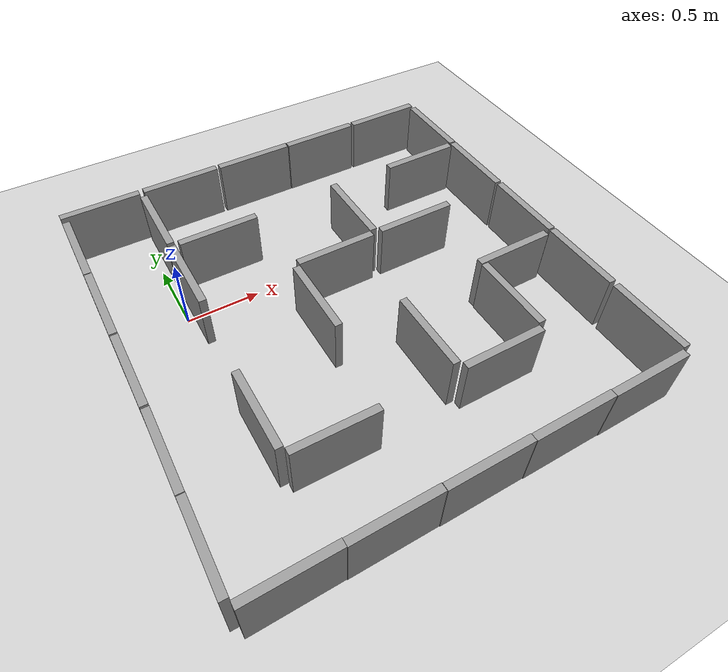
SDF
<sdf version="1.6">
 <world name="default">
  <light name="sun" type="directional">
   <pose>0 0 10 0 -0 0</pose>
   <diffuse>0.8 0.8 0.8 1</diffuse>
   <specular>0.2 0.2 0.2 1</specular>
   <attenuation>
    <range>1000</range>
    <constant>0.9</constant>
    <linear>0.01</linear>
    <quadratic>0.001</quadratic>
   </attenuation>
   <direction>-0.5 0.1 -0.9</direction>
  </light>
  <model name="ground_plane">
   <static>1</static>
   <link name="link">
    <collision name="collision">
     <geometry><plane><normal>0 0 1</normal><size>100 100</size></plane></geometry>
     <surface>
      <contact><collide_bitmask>65535</collide_bitmask></contact>
      <friction><ode><mu>100</mu><mu2>50</mu2></ode></friction>
     </surface>
    </collision>
    <visual name="visual">
     <cast_shadows>0</cast_shadows>
     <geometry><plane><normal>0 0 1</normal><size>100 100</size></plane></geometry>
     <material>
      <script><uri>file://media/materials/scripts/gazebo.material</uri><name>Gazebo/Grey</name></script>
     </material>
    </visual>
   </link>
  </model>
  <gravity>0 0 -9.8</gravity>
  <magnetic_field>6e-06 2.3e-05 -4.2e-05</magnetic_field>
  <atmosphere type="adiabatic"/>
  <physics name="default_physics" default="0" type="ode">
   <max_step_size>0.001</max_step_size>
   <real_time_factor>1</real_time_factor>
   <real_time_update_rate>1000</real_time_update_rate>
  </physics>
  <scene><ambient>0.4 0.4 0.4 1</ambient><background>0.7 0.7 0.7 1</background><shadows>1</shadows></scene>
  <audio><device>default</device></audio>
  <spherical_coordinates>
   <surface_model>EARTH_WGS84</surface_model>
   <latitude_deg>0</latitude_deg>
   <longitude_deg>0</longitude_deg>
   <elevation>0</elevation>
   <heading_deg>0</heading_deg>
  </spherical_coordinates>
  <model name="Maze_unit">
   <link name="link">
    <inertial>
     <mass>1</mass>
     <inertia>
      <ixx>0.166667</ixx>
      <ixy>0</ixy>
      <ixz>0</ixz>
      <iyy>0.166667</iyy>
      <iyz>0</iyz>
      <izz>0.166667</izz>
     </inertia>
    </inertial>
    <pose>-0.463146 -0.530916 -0 0 -0 0</pose>
    <visual name="visual">
     <geometry><box><size>0.05 0.55 0.4</size></box></geometry>
     <material>
      <script><name>Gazebo/Grey</name><uri>file://media/materials/scripts/gazebo.material</uri></script>
      <shader type="vertex"><normal_map>__default__</normal_map></shader>
      <ambient>0.3 0.3 0.3 1</ambient>
      <diffuse>0.7 0.7 0.7 1</diffuse>
      <specular>0.01 0.01 0.01 1</specular>
      <emissive>0 0 0 1</emissive>
     </material>
    </visual>
    <collision name="collision">
     <geometry><box><size>0.05 0.55 0.4</size></box></geometry>
     <surface>
      <friction>
       <ode><mu>1</mu><mu2>1</mu2><fdir1>0 0 0</fdir1><slip1>0</slip1><slip2>0</slip2></ode>
       <torsional>
        <coefficient>1</coefficient>
        <patch_radius>0</patch_radius>
        <surface_radius>0</surface_radius>
        <use_patch_radius>1</use_patch_radius>
        <ode><slip>0</slip></ode>
       </torsional>
      </friction>
      <bounce><restitution_coefficient>0</restitution_coefficient><threshold>1e+06</threshold></bounce>
      <contact>
       <collide_without_contact>0</collide_without_contact>
       <collide_without_contact_bitmask>1</collide_without_contact_bitmask>
       <collide_bitmask>1</collide_bitmask>
       <ode>
        <soft_cfm>0</soft_cfm>
        <soft_erp>0.2</soft_erp>
        <kp>1e+13</kp>
        <kd>1</kd>
        <max_vel>0.01</max_vel>
        <min_depth>0</min_depth>
       </ode>
       <bullet>
        <split_impulse>1</split_impulse>
        <split_impulse_penetration_threshold>-0.01</split_impulse_penetration_threshold>
        <soft_cfm>0</soft_cfm>
        <soft_erp>0.2</soft_erp>
        <kp>1e+13</kp>
        <kd>1</kd>
       </bullet>
      </contact>
     </surface>
    </collision>
   </link>
   <static>1</static>
   <pose>-0.01118 -1.11118 0.199993 -9e-06 -0 -0.010706</pose>
  </model>
  <model name="Maze_unit_0">
   <link name="link">
    <inertial>
     <mass>1</mass>
     <inertia>
      <ixx>0.166667</ixx>
      <ixy>0</ixy>
      <ixz>0</ixz>
      <iyy>0.166667</iyy>
      <iyz>0</iyz>
      <izz>0.166667</izz>
     </inertia>
    </inertial>
    <pose>-0.463146 -0.530916 -0 0 -0 0</pose>
    <visual name="visual">
     <geometry><box><size>0.05 0.55 0.4</size></box></geometry>
     <material>
      <script><name>Gazebo/Grey</name><uri>file://media/materials/scripts/gazebo.material</uri></script>
      <shader type="vertex"><normal_map>__default__</normal_map></shader>
      <ambient>0.3 0.3 0.3 1</ambient>
      <diffuse>0.7 0.7 0.7 1</diffuse>
      <specular>0.01 0.01 0.01 1</specular>
      <emissive>0 0 0 1</emissive>
     </material>
    </visual>
    <collision name="collision">
     <geometry><box><size>0.05 0.55 0.4</size></box></geometry>
     <surface>
      <friction>
       <ode><mu>1</mu><mu2>1</mu2><fdir1>0 0 0</fdir1><slip1>0</slip1><slip2>0</slip2></ode>
       <torsional>
        <coefficient>1</coefficient>
        <patch_radius>0</patch_radius>
        <surface_radius>0</surface_radius>
        <use_patch_radius>1</use_patch_radius>
        <ode><slip>0</slip></ode>
       </torsional>
      </friction>
      <bounce><restitution_coefficient>0</restitution_coefficient><threshold>1e+06</threshold></bounce>
      <contact>
       <collide_without_contact>0</collide_without_contact>
       <collide_without_contact_bitmask>1</collide_without_contact_bitmask>
       <collide_bitmask>1</collide_bitmask>
       <ode>
        <soft_cfm>0</soft_cfm>
        <soft_erp>0.2</soft_erp>
        <kp>1e+13</kp>
        <kd>1</kd>
        <max_vel>0.01</max_vel>
        <min_depth>0</min_depth>
       </ode>
       <bullet>
        <split_impulse>1</split_impulse>
        <split_impulse_penetration_threshold>-0.01</split_impulse_penetration_threshold>
        <soft_cfm>0</soft_cfm>
        <soft_erp>0.2</soft_erp>
        <kp>1e+13</kp>
        <kd>1</kd>
       </bullet>
      </contact>
     </surface>
    </collision>
   </link>
   <static>1</static>
   <pose>-0.006114 -0.556246 0.2 -0 -0 -0.010815</pose>
  </model>
  <model name="Maze_unit_clone">
   <link name="link">
    <inertial>
     <mass>1</mass>
     <inertia>
      <ixx>0.166667</ixx>
      <ixy>0</ixy>
      <ixz>0</ixz>
      <iyy>0.166667</iyy>
      <iyz>0</iyz>
      <izz>0.166667</izz>
     </inertia>
    </inertial>
    <pose>-0.463146 -0.530916 -0 0 -0 0</pose>
    <visual name="visual">
     <geometry><box><size>0.05 0.55 0.4</size></box></geometry>
     <material>
      <script><name>Gazebo/Grey</name><uri>file://media/materials/scripts/gazebo.material</uri></script>
      <shader type="vertex"><normal_map>__default__</normal_map></shader>
      <ambient>0.3 0.3 0.3 1</ambient>
      <diffuse>0.7 0.7 0.7 1</diffuse>
      <specular>0.01 0.01 0.01 1</specular>
      <emissive>0 0 0 1</emissive>
     </material>
    </visual>
    <collision name="collision">
     <geometry><box><size>0.05 0.55 0.4</size></box></geometry>
     <surface>
      <friction>
       <ode><mu>1</mu><mu2>1</mu2><fdir1>0 0 0</fdir1><slip1>0</slip1><slip2>0</slip2></ode>
       <torsional>
        <coefficient>1</coefficient>
        <patch_radius>0</patch_radius>
        <surface_radius>0</surface_radius>
        <use_patch_radius>1</use_patch_radius>
        <ode><slip>0</slip></ode>
       </torsional>
      </friction>
      <bounce><restitution_coefficient>0</restitution_coefficient><threshold>1e+06</threshold></bounce>
      <contact>
       <collide_without_contact>0</collide_without_contact>
       <collide_without_contact_bitmask>1</collide_without_contact_bitmask>
       <collide_bitmask>1</collide_bitmask>
       <ode>
        <soft_cfm>0</soft_cfm>
        <soft_erp>0.2</soft_erp>
        <kp>1e+13</kp>
        <kd>1</kd>
        <max_vel>0.01</max_vel>
        <min_depth>0</min_depth>
       </ode>
       <bullet>
        <split_impulse>1</split_impulse>
        <split_impulse_penetration_threshold>-0.01</split_impulse_penetration_threshold>
        <soft_cfm>0</soft_cfm>
        <soft_erp>0.2</soft_erp>
        <kp>1e+13</kp>
        <kd>1</kd>
       </bullet>
      </contact>
     </surface>
    </collision>
   </link>
   <static>1</static>
   <pose>-0.009404 0.011997 0.2 -0 -0 -0.000526</pose>
  </model>
  <model name="Maze_unit_clone_0">
   <link name="link">
    <inertial>
     <mass>1</mass>
     <inertia>
      <ixx>0.166667</ixx>
      <ixy>0</ixy>
      <ixz>0</ixz>
      <iyy>0.166667</iyy>
      <iyz>0</iyz>
      <izz>0.166667</izz>
     </inertia>
    </inertial>
    <pose>-0.463146 -0.530916 -0 0 -0 0</pose>
    <visual name="visual">
     <geometry><box><size>0.05 0.55 0.4</size></box></geometry>
     <material>
      <script><name>Gazebo/Grey</name><uri>file://media/materials/scripts/gazebo.material</uri></script>
      <shader type="vertex"><normal_map>__default__</normal_map></shader>
      <ambient>0.3 0.3 0.3 1</ambient>
      <diffuse>0.7 0.7 0.7 1</diffuse>
      <specular>0.01 0.01 0.01 1</specular>
      <emissive>0 0 0 1</emissive>
     </material>
    </visual>
    <collision name="collision">
     <geometry><box><size>0.05 0.55 0.4</size></box></geometry>
     <surface>
      <friction>
       <ode><mu>1</mu><mu2>1</mu2><fdir1>0 0 0</fdir1><slip1>0</slip1><slip2>0</slip2></ode>
       <torsional>
        <coefficient>1</coefficient>
        <patch_radius>0</patch_radius>
        <surface_radius>0</surface_radius>
        <use_patch_radius>1</use_patch_radius>
        <ode><slip>0</slip></ode>
       </torsional>
      </friction>
      <bounce><restitution_coefficient>0</restitution_coefficient><threshold>1e+06</threshold></bounce>
      <contact>
       <collide_without_contact>0</collide_without_contact>
       <collide_without_contact_bitmask>1</collide_without_contact_bitmask>
       <collide_bitmask>1</collide_bitmask>
       <ode>
        <soft_cfm>0</soft_cfm>
        <soft_erp>0.2</soft_erp>
        <kp>1e+13</kp>
        <kd>1</kd>
        <max_vel>0.01</max_vel>
        <min_depth>0</min_depth>
       </ode>
       <bullet>
        <split_impulse>1</split_impulse>
        <split_impulse_penetration_threshold>-0.01</split_impulse_penetration_threshold>
        <soft_cfm>0</soft_cfm>
        <soft_erp>0.2</soft_erp>
        <kp>1e+13</kp>
        <kd>1</kd>
       </bullet>
      </contact>
     </surface>
    </collision>
   </link>
   <static>1</static>
   <pose>-0.010054 0.572677 0.2 1e-06 1e-06 -0.00027</pose>
  </model>
  <model name="Maze_unit_clone_1">
   <link name="link">
    <inertial>
     <mass>1</mass>
     <inertia>
      <ixx>0.166667</ixx>
      <ixy>0</ixy>
      <ixz>0</ixz>
      <iyy>0.166667</iyy>
      <iyz>0</iyz>
      <izz>0.166667</izz>
     </inertia>
    </inertial>
    <pose>-0.463146 -0.530916 -0 0 -0 0</pose>
    <visual name="visual">
     <geometry><box><size>0.05 0.55 0.4</size></box></geometry>
     <material>
      <script><name>Gazebo/Grey</name><uri>file://media/materials/scripts/gazebo.material</uri></script>
      <shader type="vertex"><normal_map>__default__</normal_map></shader>
      <ambient>0.3 0.3 0.3 1</ambient>
      <diffuse>0.7 0.7 0.7 1</diffuse>
      <specular>0.01 0.01 0.01 1</specular>
      <emissive>0 0 0 1</emissive>
     </material>
    </visual>
    <collision name="collision">
     <geometry><box><size>0.05 0.55 0.4</size></box></geometry>
     <surface>
      <friction>
       <ode><mu>1</mu><mu2>1</mu2><fdir1>0 0 0</fdir1><slip1>0</slip1><slip2>0</slip2></ode>
       <torsional>
        <coefficient>1</coefficient>
        <patch_radius>0</patch_radius>
        <surface_radius>0</surface_radius>
        <use_patch_radius>1</use_patch_radius>
        <ode><slip>0</slip></ode>
       </torsional>
      </friction>
      <bounce><restitution_coefficient>0</restitution_coefficient><threshold>1e+06</threshold></bounce>
      <contact>
       <collide_without_contact>0</collide_without_contact>
       <collide_without_contact_bitmask>1</collide_without_contact_bitmask>
       <collide_bitmask>1</collide_bitmask>
       <ode>
        <soft_cfm>0</soft_cfm>
        <soft_erp>0.2</soft_erp>
        <kp>1e+13</kp>
        <kd>1</kd>
        <max_vel>0.01</max_vel>
        <min_depth>0</min_depth>
       </ode>
       <bullet>
        <split_impulse>1</split_impulse>
        <split_impulse_penetration_threshold>-0.01</split_impulse_penetration_threshold>
        <soft_cfm>0</soft_cfm>
        <soft_erp>0.2</soft_erp>
        <kp>1e+13</kp>
        <kd>1</kd>
       </bullet>
      </contact>
     </surface>
    </collision>
   </link>
   <static>1</static>
   <pose>-0.010091 1.1268 0.2 0 0 -0.000544</pose>
  </model>
  <model name="Maze_unit_clone_2">
   <link name="link">
    <inertial>
     <mass>1</mass>
     <inertia>
      <ixx>0.166667</ixx>
      <ixy>0</ixy>
      <ixz>0</ixz>
      <iyy>0.166667</iyy>
      <iyz>0</iyz>
      <izz>0.166667</izz>
     </inertia>
    </inertial>
    <pose>-0.463146 -0.530916 -0 0 -0 0</pose>
    <visual name="visual">
     <geometry><box><size>0.05 0.55 0.4</size></box></geometry>
     <material>
      <script><name>Gazebo/Grey</name><uri>file://media/materials/scripts/gazebo.material</uri></script>
      <shader type="vertex"><normal_map>__default__</normal_map></shader>
      <ambient>0.3 0.3 0.3 1</ambient>
      <diffuse>0.7 0.7 0.7 1</diffuse>
      <specular>0.01 0.01 0.01 1</specular>
      <emissive>0 0 0 1</emissive>
     </material>
    </visual>
    <collision name="collision">
     <geometry><box><size>0.05 0.55 0.4</size></box></geometry>
     <surface>
      <friction>
       <ode><mu>1</mu><mu2>1</mu2><fdir1>0 0 0</fdir1><slip1>0</slip1><slip2>0</slip2></ode>
       <torsional>
        <coefficient>1</coefficient>
        <patch_radius>0</patch_radius>
        <surface_radius>0</surface_radius>
        <use_patch_radius>1</use_patch_radius>
        <ode><slip>0</slip></ode>
       </torsional>
      </friction>
      <bounce><restitution_coefficient>0</restitution_coefficient><threshold>1e+06</threshold></bounce>
      <contact>
       <collide_without_contact>0</collide_without_contact>
       <collide_without_contact_bitmask>1</collide_without_contact_bitmask>
       <collide_bitmask>1</collide_bitmask>
       <ode>
        <soft_cfm>0</soft_cfm>
        <soft_erp>0.2</soft_erp>
        <kp>1e+13</kp>
        <kd>1</kd>
        <max_vel>0.01</max_vel>
        <min_depth>0</min_depth>
       </ode>
       <bullet>
        <split_impulse>1</split_impulse>
        <split_impulse_penetration_threshold>-0.01</split_impulse_penetration_threshold>
        <soft_cfm>0</soft_cfm>
        <soft_erp>0.2</soft_erp>
        <kp>1e+13</kp>
        <kd>1</kd>
       </bullet>
      </contact>
     </surface>
    </collision>
   </link>
   <static>1</static>
   <pose>0.496874 -0.561027 0.2 0 -0 0.006084</pose>
  </model>
  <model name="Maze_unit_clone_3">
   <link name="link">
    <inertial>
     <mass>1</mass>
     <inertia>
      <ixx>0.166667</ixx>
      <ixy>0</ixy>
      <ixz>0</ixz>
      <iyy>0.166667</iyy>
      <iyz>0</iyz>
      <izz>0.166667</izz>
     </inertia>
    </inertial>
    <pose>-0.463146 -0.530916 -0 0 -0 0</pose>
    <visual name="visual">
     <geometry><box><size>0.05 0.55 0.4</size></box></geometry>
     <material>
      <script><name>Gazebo/Grey</name><uri>file://media/materials/scripts/gazebo.material</uri></script>
      <shader type="vertex"><normal_map>__default__</normal_map></shader>
      <ambient>0.3 0.3 0.3 1</ambient>
      <diffuse>0.7 0.7 0.7 1</diffuse>
      <specular>0.01 0.01 0.01 1</specular>
      <emissive>0 0 0 1</emissive>
     </material>
    </visual>
    <collision name="collision">
     <geometry><box><size>0.05 0.55 0.4</size></box></geometry>
     <surface>
      <friction>
       <ode><mu>1</mu><mu2>1</mu2><fdir1>0 0 0</fdir1><slip1>0</slip1><slip2>0</slip2></ode>
       <torsional>
        <coefficient>1</coefficient>
        <patch_radius>0</patch_radius>
        <surface_radius>0</surface_radius>
        <use_patch_radius>1</use_patch_radius>
        <ode><slip>0</slip></ode>
       </torsional>
      </friction>
      <bounce><restitution_coefficient>0</restitution_coefficient><threshold>1e+06</threshold></bounce>
      <contact>
       <collide_without_contact>0</collide_without_contact>
       <collide_without_contact_bitmask>1</collide_without_contact_bitmask>
       <collide_bitmask>1</collide_bitmask>
       <ode>
        <soft_cfm>0</soft_cfm>
        <soft_erp>0.2</soft_erp>
        <kp>1e+13</kp>
        <kd>1</kd>
        <max_vel>0.01</max_vel>
        <min_depth>0</min_depth>
       </ode>
       <bullet>
        <split_impulse>1</split_impulse>
        <split_impulse_penetration_threshold>-0.01</split_impulse_penetration_threshold>
        <soft_cfm>0</soft_cfm>
        <soft_erp>0.2</soft_erp>
        <kp>1e+13</kp>
        <kd>1</kd>
       </bullet>
      </contact>
     </surface>
    </collision>
   </link>
   <static>1</static>
   <pose>0.530974 0.559352 0.2 0 -0 0.000106</pose>
  </model>
  <model name="Maze_unit_clone_4">
   <link name="link">
    <inertial>
     <mass>1</mass>
     <inertia>
      <ixx>0.166667</ixx>
      <ixy>0</ixy>
      <ixz>0</ixz>
      <iyy>0.166667</iyy>
      <iyz>0</iyz>
      <izz>0.166667</izz>
     </inertia>
    </inertial>
    <pose>-0.463146 -0.530916 -0 0 -0 0</pose>
    <visual name="visual">
     <geometry><box><size>0.05 0.55 0.4</size></box></geometry>
     <material>
      <script><name>Gazebo/Grey</name><uri>file://media/materials/scripts/gazebo.material</uri></script>
      <shader type="vertex"><normal_map>__default__</normal_map></shader>
      <ambient>0.3 0.3 0.3 1</ambient>
      <diffuse>0.7 0.7 0.7 1</diffuse>
      <specular>0.01 0.01 0.01 1</specular>
      <emissive>0 0 0 1</emissive>
     </material>
    </visual>
    <collision name="collision">
     <geometry><box><size>0.05 0.55 0.4</size></box></geometry>
     <surface>
      <friction>
       <ode><mu>1</mu><mu2>1</mu2><fdir1>0 0 0</fdir1><slip1>0</slip1><slip2>0</slip2></ode>
       <torsional>
        <coefficient>1</coefficient>
        <patch_radius>0</patch_radius>
        <surface_radius>0</surface_radius>
        <use_patch_radius>1</use_patch_radius>
        <ode><slip>0</slip></ode>
       </torsional>
      </friction>
      <bounce><restitution_coefficient>0</restitution_coefficient><threshold>1e+06</threshold></bounce>
      <contact>
       <collide_without_contact>0</collide_without_contact>
       <collide_without_contact_bitmask>1</collide_without_contact_bitmask>
       <collide_bitmask>1</collide_bitmask>
       <ode>
        <soft_cfm>0</soft_cfm>
        <soft_erp>0.2</soft_erp>
        <kp>1e+13</kp>
        <kd>1</kd>
        <max_vel>0.01</max_vel>
        <min_depth>0</min_depth>
       </ode>
       <bullet>
        <split_impulse>1</split_impulse>
        <split_impulse_penetration_threshold>-0.01</split_impulse_penetration_threshold>
        <soft_cfm>0</soft_cfm>
        <soft_erp>0.2</soft_erp>
        <kp>1e+13</kp>
        <kd>1</kd>
       </bullet>
      </contact>
     </surface>
    </collision>
   </link>
   <static>1</static>
   <pose>0.53227 1.1388 0.199993 -9e-06 -0 0.001029</pose>
  </model>
  <model name="Maze_unit_clone_5">
   <link name="link">
    <inertial>
     <mass>1</mass>
     <inertia>
      <ixx>0.166667</ixx>
      <ixy>0</ixy>
      <ixz>0</ixz>
      <iyy>0.166667</iyy>
      <iyz>0</iyz>
      <izz>0.166667</izz>
     </inertia>
    </inertial>
    <pose>-0.463146 -0.530916 -0 0 -0 0</pose>
    <visual name="visual">
     <geometry><box><size>0.05 0.55 0.4</size></box></geometry>
     <material>
      <script><name>Gazebo/Grey</name><uri>file://media/materials/scripts/gazebo.material</uri></script>
      <shader type="vertex"><normal_map>__default__</normal_map></shader>
      <ambient>0.3 0.3 0.3 1</ambient>
      <diffuse>0.7 0.7 0.7 1</diffuse>
      <specular>0.01 0.01 0.01 1</specular>
      <emissive>0 0 0 1</emissive>
     </material>
    </visual>
    <collision name="collision">
     <geometry><box><size>0.05 0.55 0.4</size></box></geometry>
     <surface>
      <friction>
       <ode><mu>1</mu><mu2>1</mu2><fdir1>0 0 0</fdir1><slip1>0</slip1><slip2>0</slip2></ode>
       <torsional>
        <coefficient>1</coefficient>
        <patch_radius>0</patch_radius>
        <surface_radius>0</surface_radius>
        <use_patch_radius>1</use_patch_radius>
        <ode><slip>0</slip></ode>
       </torsional>
      </friction>
      <bounce><restitution_coefficient>0</restitution_coefficient><threshold>1e+06</threshold></bounce>
      <contact>
       <collide_without_contact>0</collide_without_contact>
       <collide_without_contact_bitmask>1</collide_without_contact_bitmask>
       <collide_bitmask>1</collide_bitmask>
       <ode>
        <soft_cfm>0</soft_cfm>
        <soft_erp>0.2</soft_erp>
        <kp>1e+13</kp>
        <kd>1</kd>
        <max_vel>0.01</max_vel>
        <min_depth>0</min_depth>
       </ode>
       <bullet>
        <split_impulse>1</split_impulse>
        <split_impulse_penetration_threshold>-0.01</split_impulse_penetration_threshold>
        <soft_cfm>0</soft_cfm>
        <soft_erp>0.2</soft_erp>
        <kp>1e+13</kp>
        <kd>1</kd>
       </bullet>
      </contact>
     </surface>
    </collision>
   </link>
   <static>1</static>
   <pose>-0.718563 -1.48869 0.200001 0 -2e-06 1.5766</pose>
  </model>
  <model name="Maze_unit_clone_5_clone">
   <link name="link">
    <inertial>
     <mass>1</mass>
     <inertia>
      <ixx>0.166667</ixx>
      <ixy>0</ixy>
      <ixz>0</ixz>
      <iyy>0.166667</iyy>
      <iyz>0</iyz>
      <izz>0.166667</izz>
     </inertia>
    </inertial>
    <pose>-0.463146 -0.530916 -0 0 -0 0</pose>
    <visual name="visual">
     <geometry><box><size>0.05 0.55 0.4</size></box></geometry>
     <material>
      <script><name>Gazebo/Grey</name><uri>file://media/materials/scripts/gazebo.material</uri></script>
      <shader type="vertex"><normal_map>__default__</normal_map></shader>
      <ambient>0.3 0.3 0.3 1</ambient>
      <diffuse>0.7 0.7 0.7 1</diffuse>
      <specular>0.01 0.01 0.01 1</specular>
      <emissive>0 0 0 1</emissive>
     </material>
    </visual>
    <collision name="collision">
     <geometry><box><size>0.05 0.55 0.4</size></box></geometry>
     <surface>
      <friction>
       <ode><mu>1</mu><mu2>1</mu2><fdir1>0 0 0</fdir1><slip1>0</slip1><slip2>0</slip2></ode>
       <torsional>
        <coefficient>1</coefficient>
        <patch_radius>0</patch_radius>
        <surface_radius>0</surface_radius>
        <use_patch_radius>1</use_patch_radius>
        <ode><slip>0</slip></ode>
       </torsional>
      </friction>
      <bounce><restitution_coefficient>0</restitution_coefficient><threshold>1e+06</threshold></bounce>
      <contact>
       <collide_without_contact>0</collide_without_contact>
       <collide_without_contact_bitmask>1</collide_without_contact_bitmask>
       <collide_bitmask>1</collide_bitmask>
       <ode>
        <soft_cfm>0</soft_cfm>
        <soft_erp>0.2</soft_erp>
        <kp>1e+13</kp>
        <kd>1</kd>
        <max_vel>0.01</max_vel>
        <min_depth>0</min_depth>
       </ode>
       <bullet>
        <split_impulse>1</split_impulse>
        <split_impulse_penetration_threshold>-0.01</split_impulse_penetration_threshold>
        <soft_cfm>0</soft_cfm>
        <soft_erp>0.2</soft_erp>
        <kp>1e+13</kp>
        <kd>1</kd>
       </bullet>
      </contact>
     </surface>
    </collision>
   </link>
   <static>1</static>
   <pose>-0.168545 -1.48859 0.200001 0 -2e-06 1.5766</pose>
  </model>
  <model name="Maze_unit_clone_5_clone_0">
   <link name="link">
    <inertial>
     <mass>1</mass>
     <inertia>
      <ixx>0.166667</ixx>
      <ixy>0</ixy>
      <ixz>0</ixz>
      <iyy>0.166667</iyy>
      <iyz>0</iyz>
      <izz>0.166667</izz>
     </inertia>
    </inertial>
    <pose>-0.463146 -0.530916 -0 0 -0 0</pose>
    <visual name="visual">
     <geometry><box><size>0.05 0.55 0.4</size></box></geometry>
     <material>
      <script><name>Gazebo/Grey</name><uri>file://media/materials/scripts/gazebo.material</uri></script>
      <shader type="vertex"><normal_map>__default__</normal_map></shader>
      <ambient>0.3 0.3 0.3 1</ambient>
      <diffuse>0.7 0.7 0.7 1</diffuse>
      <specular>0.01 0.01 0.01 1</specular>
      <emissive>0 0 0 1</emissive>
     </material>
    </visual>
    <collision name="collision">
     <geometry><box><size>0.05 0.55 0.4</size></box></geometry>
     <surface>
      <friction>
       <ode><mu>1</mu><mu2>1</mu2><fdir1>0 0 0</fdir1><slip1>0</slip1><slip2>0</slip2></ode>
       <torsional>
        <coefficient>1</coefficient>
        <patch_radius>0</patch_radius>
        <surface_radius>0</surface_radius>
        <use_patch_radius>1</use_patch_radius>
        <ode><slip>0</slip></ode>
       </torsional>
      </friction>
      <bounce><restitution_coefficient>0</restitution_coefficient><threshold>1e+06</threshold></bounce>
      <contact>
       <collide_without_contact>0</collide_without_contact>
       <collide_without_contact_bitmask>1</collide_without_contact_bitmask>
       <collide_bitmask>1</collide_bitmask>
       <ode>
        <soft_cfm>0</soft_cfm>
        <soft_erp>0.2</soft_erp>
        <kp>1e+13</kp>
        <kd>1</kd>
        <max_vel>0.01</max_vel>
        <min_depth>0</min_depth>
       </ode>
       <bullet>
        <split_impulse>1</split_impulse>
        <split_impulse_penetration_threshold>-0.01</split_impulse_penetration_threshold>
        <soft_cfm>0</soft_cfm>
        <soft_erp>0.2</soft_erp>
        <kp>1e+13</kp>
        <kd>1</kd>
       </bullet>
      </contact>
     </surface>
    </collision>
   </link>
   <static>1</static>
   <pose>0.382806 -1.48868 0.200002 -0 -5e-06 1.57668</pose>
  </model>
  <model name="Maze_unit_clone_5_clone_1">
   <link name="link">
    <inertial>
     <mass>1</mass>
     <inertia>
      <ixx>0.166667</ixx>
      <ixy>0</ixy>
      <ixz>0</ixz>
      <iyy>0.166667</iyy>
      <iyz>0</iyz>
      <izz>0.166667</izz>
     </inertia>
    </inertial>
    <pose>-0.463146 -0.530916 -0 0 -0 0</pose>
    <visual name="visual">
     <geometry><box><size>0.05 0.55 0.4</size></box></geometry>
     <material>
      <script><name>Gazebo/Grey</name><uri>file://media/materials/scripts/gazebo.material</uri></script>
      <shader type="vertex"><normal_map>__default__</normal_map></shader>
      <ambient>0.3 0.3 0.3 1</ambient>
      <diffuse>0.7 0.7 0.7 1</diffuse>
      <specular>0.01 0.01 0.01 1</specular>
      <emissive>0 0 0 1</emissive>
     </material>
    </visual>
    <collision name="collision">
     <geometry><box><size>0.05 0.55 0.4</size></box></geometry>
     <surface>
      <friction>
       <ode><mu>1</mu><mu2>1</mu2><fdir1>0 0 0</fdir1><slip1>0</slip1><slip2>0</slip2></ode>
       <torsional>
        <coefficient>1</coefficient>
        <patch_radius>0</patch_radius>
        <surface_radius>0</surface_radius>
        <use_patch_radius>1</use_patch_radius>
        <ode><slip>0</slip></ode>
       </torsional>
      </friction>
      <bounce><restitution_coefficient>0</restitution_coefficient><threshold>1e+06</threshold></bounce>
      <contact>
       <collide_without_contact>0</collide_without_contact>
       <collide_without_contact_bitmask>1</collide_without_contact_bitmask>
       <collide_bitmask>1</collide_bitmask>
       <ode>
        <soft_cfm>0</soft_cfm>
        <soft_erp>0.2</soft_erp>
        <kp>1e+13</kp>
        <kd>1</kd>
        <max_vel>0.01</max_vel>
        <min_depth>0</min_depth>
       </ode>
       <bullet>
        <split_impulse>1</split_impulse>
        <split_impulse_penetration_threshold>-0.01</split_impulse_penetration_threshold>
        <soft_cfm>0</soft_cfm>
        <soft_erp>0.2</soft_erp>
        <kp>1e+13</kp>
        <kd>1</kd>
       </bullet>
      </contact>
     </surface>
    </collision>
   </link>
   <static>1</static>
   <pose>0.932909 -1.48862 0.199997 -0 6e-06 1.57653</pose>
  </model>
  <model name="Maze_unit_clone_5_clone_2">
   <link name="link">
    <inertial>
     <mass>1</mass>
     <inertia>
      <ixx>0.166667</ixx>
      <ixy>0</ixy>
      <ixz>0</ixz>
      <iyy>0.166667</iyy>
      <iyz>0</iyz>
      <izz>0.166667</izz>
     </inertia>
    </inertial>
    <pose>-0.463146 -0.530916 -0 0 -0 0</pose>
    <visual name="visual">
     <geometry><box><size>0.05 0.55 0.4</size></box></geometry>
     <material>
      <script><name>Gazebo/Grey</name><uri>file://media/materials/scripts/gazebo.material</uri></script>
      <shader type="vertex"><normal_map>__default__</normal_map></shader>
      <ambient>0.3 0.3 0.3 1</ambient>
      <diffuse>0.7 0.7 0.7 1</diffuse>
      <specular>0.01 0.01 0.01 1</specular>
      <emissive>0 0 0 1</emissive>
     </material>
    </visual>
    <collision name="collision">
     <geometry><box><size>0.05 0.55 0.4</size></box></geometry>
     <surface>
      <friction>
       <ode><mu>1</mu><mu2>1</mu2><fdir1>0 0 0</fdir1><slip1>0</slip1><slip2>0</slip2></ode>
       <torsional>
        <coefficient>1</coefficient>
        <patch_radius>0</patch_radius>
        <surface_radius>0</surface_radius>
        <use_patch_radius>1</use_patch_radius>
        <ode><slip>0</slip></ode>
       </torsional>
      </friction>
      <bounce><restitution_coefficient>0</restitution_coefficient><threshold>1e+06</threshold></bounce>
      <contact>
       <collide_without_contact>0</collide_without_contact>
       <collide_without_contact_bitmask>1</collide_without_contact_bitmask>
       <collide_bitmask>1</collide_bitmask>
       <ode>
        <soft_cfm>0</soft_cfm>
        <soft_erp>0.2</soft_erp>
        <kp>1e+13</kp>
        <kd>1</kd>
        <max_vel>0.01</max_vel>
        <min_depth>0</min_depth>
       </ode>
       <bullet>
        <split_impulse>1</split_impulse>
        <split_impulse_penetration_threshold>-0.01</split_impulse_penetration_threshold>
        <soft_cfm>0</soft_cfm>
        <soft_erp>0.2</soft_erp>
        <kp>1e+13</kp>
        <kd>1</kd>
       </bullet>
      </contact>
     </surface>
    </collision>
   </link>
   <static>1</static>
   <pose>1.48286 -1.48866 0.2 0 -0 1.57668</pose>
  </model>
  <model name="Maze_unit_clone_5_clone_3">
   <link name="link">
    <inertial>
     <mass>1</mass>
     <inertia>
      <ixx>0.166667</ixx>
      <ixy>0</ixy>
      <ixz>0</ixz>
      <iyy>0.166667</iyy>
      <iyz>0</iyz>
      <izz>0.166667</izz>
     </inertia>
    </inertial>
    <pose>-0.463146 -0.530916 -0 0 -0 0</pose>
    <visual name="visual">
     <geometry><box><size>0.05 0.55 0.4</size></box></geometry>
     <material>
      <script><name>Gazebo/Grey</name><uri>file://media/materials/scripts/gazebo.material</uri></script>
      <shader type="vertex"><normal_map>__default__</normal_map></shader>
      <ambient>0.3 0.3 0.3 1</ambient>
      <diffuse>0.7 0.7 0.7 1</diffuse>
      <specular>0.01 0.01 0.01 1</specular>
      <emissive>0 0 0 1</emissive>
     </material>
    </visual>
    <collision name="collision">
     <geometry><box><size>0.05 0.55 0.4</size></box></geometry>
     <surface>
      <friction>
       <ode><mu>1</mu><mu2>1</mu2><fdir1>0 0 0</fdir1><slip1>0</slip1><slip2>0</slip2></ode>
       <torsional>
        <coefficient>1</coefficient>
        <patch_radius>0</patch_radius>
        <surface_radius>0</surface_radius>
        <use_patch_radius>1</use_patch_radius>
        <ode><slip>0</slip></ode>
       </torsional>
      </friction>
      <bounce><restitution_coefficient>0</restitution_coefficient><threshold>1e+06</threshold></bounce>
      <contact>
       <collide_without_contact>0</collide_without_contact>
       <collide_without_contact_bitmask>1</collide_without_contact_bitmask>
       <collide_bitmask>1</collide_bitmask>
       <ode>
        <soft_cfm>0</soft_cfm>
        <soft_erp>0.2</soft_erp>
        <kp>1e+13</kp>
        <kd>1</kd>
        <max_vel>0.01</max_vel>
        <min_depth>0</min_depth>
       </ode>
       <bullet>
        <split_impulse>1</split_impulse>
        <split_impulse_penetration_threshold>-0.01</split_impulse_penetration_threshold>
        <soft_cfm>0</soft_cfm>
        <soft_erp>0.2</soft_erp>
        <kp>1e+13</kp>
        <kd>1</kd>
       </bullet>
      </contact>
     </surface>
    </collision>
   </link>
   <static>1</static>
   <pose>-0.752801 1.40494 0.2 0 1e-06 1.57111</pose>
  </model>
  <model name="Maze_unit_clone_5_clone_4">
   <link name="link">
    <inertial>
     <mass>1</mass>
     <inertia>
      <ixx>0.166667</ixx>
      <ixy>0</ixy>
      <ixz>0</ixz>
      <iyy>0.166667</iyy>
      <iyz>0</iyz>
      <izz>0.166667</izz>
     </inertia>
    </inertial>
    <pose>-0.463146 -0.530916 -0 0 -0 0</pose>
    <visual name="visual">
     <geometry><box><size>0.05 0.55 0.4</size></box></geometry>
     <material>
      <script><name>Gazebo/Grey</name><uri>file://media/materials/scripts/gazebo.material</uri></script>
      <shader type="vertex"><normal_map>__default__</normal_map></shader>
      <ambient>0.3 0.3 0.3 1</ambient>
      <diffuse>0.7 0.7 0.7 1</diffuse>
      <specular>0.01 0.01 0.01 1</specular>
      <emissive>0 0 0 1</emissive>
     </material>
    </visual>
    <collision name="collision">
     <geometry><box><size>0.05 0.55 0.4</size></box></geometry>
     <surface>
      <friction>
       <ode><mu>1</mu><mu2>1</mu2><fdir1>0 0 0</fdir1><slip1>0</slip1><slip2>0</slip2></ode>
       <torsional>
        <coefficient>1</coefficient>
        <patch_radius>0</patch_radius>
        <surface_radius>0</surface_radius>
        <use_patch_radius>1</use_patch_radius>
        <ode><slip>0</slip></ode>
       </torsional>
      </friction>
      <bounce><restitution_coefficient>0</restitution_coefficient><threshold>1e+06</threshold></bounce>
      <contact>
       <collide_without_contact>0</collide_without_contact>
       <collide_without_contact_bitmask>1</collide_without_contact_bitmask>
       <collide_bitmask>1</collide_bitmask>
       <ode>
        <soft_cfm>0</soft_cfm>
        <soft_erp>0.2</soft_erp>
        <kp>1e+13</kp>
        <kd>1</kd>
        <max_vel>0.01</max_vel>
        <min_depth>0</min_depth>
       </ode>
       <bullet>
        <split_impulse>1</split_impulse>
        <split_impulse_penetration_threshold>-0.01</split_impulse_penetration_threshold>
        <soft_cfm>0</soft_cfm>
        <soft_erp>0.2</soft_erp>
        <kp>1e+13</kp>
        <kd>1</kd>
       </bullet>
      </contact>
     </surface>
    </collision>
   </link>
   <static>1</static>
   <pose>-0.172312 1.40639 0.2 0 -0 1.57606</pose>
  </model>
  <model name="Maze_unit_clone_5_clone_5">
   <link name="link">
    <inertial>
     <mass>1</mass>
     <inertia>
      <ixx>0.166667</ixx>
      <ixy>0</ixy>
      <ixz>0</ixz>
      <iyy>0.166667</iyy>
      <iyz>0</iyz>
      <izz>0.166667</izz>
     </inertia>
    </inertial>
    <pose>-0.463146 -0.530916 -0 0 -0 0</pose>
    <visual name="visual">
     <geometry><box><size>0.05 0.55 0.4</size></box></geometry>
     <material>
      <script><name>Gazebo/Grey</name><uri>file://media/materials/scripts/gazebo.material</uri></script>
      <shader type="vertex"><normal_map>__default__</normal_map></shader>
      <ambient>0.3 0.3 0.3 1</ambient>
      <diffuse>0.7 0.7 0.7 1</diffuse>
      <specular>0.01 0.01 0.01 1</specular>
      <emissive>0 0 0 1</emissive>
     </material>
    </visual>
    <collision name="collision">
     <geometry><box><size>0.05 0.55 0.4</size></box></geometry>
     <surface>
      <friction>
       <ode><mu>1</mu><mu2>1</mu2><fdir1>0 0 0</fdir1><slip1>0</slip1><slip2>0</slip2></ode>
       <torsional>
        <coefficient>1</coefficient>
        <patch_radius>0</patch_radius>
        <surface_radius>0</surface_radius>
        <use_patch_radius>1</use_patch_radius>
        <ode><slip>0</slip></ode>
       </torsional>
      </friction>
      <bounce><restitution_coefficient>0</restitution_coefficient><threshold>1e+06</threshold></bounce>
      <contact>
       <collide_without_contact>0</collide_without_contact>
       <collide_without_contact_bitmask>1</collide_without_contact_bitmask>
       <collide_bitmask>1</collide_bitmask>
       <ode>
        <soft_cfm>0</soft_cfm>
        <soft_erp>0.2</soft_erp>
        <kp>1e+13</kp>
        <kd>1</kd>
        <max_vel>0.01</max_vel>
        <min_depth>0</min_depth>
       </ode>
       <bullet>
        <split_impulse>1</split_impulse>
        <split_impulse_penetration_threshold>-0.01</split_impulse_penetration_threshold>
        <soft_cfm>0</soft_cfm>
        <soft_erp>0.2</soft_erp>
        <kp>1e+13</kp>
        <kd>1</kd>
       </bullet>
      </contact>
     </surface>
    </collision>
   </link>
   <static>1</static>
   <pose>0.401259 1.40639 0.200002 9e-06 -0 1.57639</pose>
  </model>
  <model name="Maze_unit_clone_5_clone_6">
   <link name="link">
    <inertial>
     <mass>1</mass>
     <inertia>
      <ixx>0.166667</ixx>
      <ixy>0</ixy>
      <ixz>0</ixz>
      <iyy>0.166667</iyy>
      <iyz>0</iyz>
      <izz>0.166667</izz>
     </inertia>
    </inertial>
    <pose>-0.463146 -0.530916 -0 0 -0 0</pose>
    <visual name="visual">
     <geometry><box><size>0.05 0.55 0.4</size></box></geometry>
     <material>
      <script><name>Gazebo/Grey</name><uri>file://media/materials/scripts/gazebo.material</uri></script>
      <shader type="vertex"><normal_map>__default__</normal_map></shader>
      <ambient>0.3 0.3 0.3 1</ambient>
      <diffuse>0.7 0.7 0.7 1</diffuse>
      <specular>0.01 0.01 0.01 1</specular>
      <emissive>0 0 0 1</emissive>
     </material>
    </visual>
    <collision name="collision">
     <geometry><box><size>0.05 0.55 0.4</size></box></geometry>
     <surface>
      <friction>
       <ode><mu>1</mu><mu2>1</mu2><fdir1>0 0 0</fdir1><slip1>0</slip1><slip2>0</slip2></ode>
       <torsional>
        <coefficient>1</coefficient>
        <patch_radius>0</patch_radius>
        <surface_radius>0</surface_radius>
        <use_patch_radius>1</use_patch_radius>
        <ode><slip>0</slip></ode>
       </torsional>
      </friction>
      <bounce><restitution_coefficient>0</restitution_coefficient><threshold>1e+06</threshold></bounce>
      <contact>
       <collide_without_contact>0</collide_without_contact>
       <collide_without_contact_bitmask>1</collide_without_contact_bitmask>
       <collide_bitmask>1</collide_bitmask>
       <ode>
        <soft_cfm>0</soft_cfm>
        <soft_erp>0.2</soft_erp>
        <kp>1e+13</kp>
        <kd>1</kd>
        <max_vel>0.01</max_vel>
        <min_depth>0</min_depth>
       </ode>
       <bullet>
        <split_impulse>1</split_impulse>
        <split_impulse_penetration_threshold>-0.01</split_impulse_penetration_threshold>
        <soft_cfm>0</soft_cfm>
        <soft_erp>0.2</soft_erp>
        <kp>1e+13</kp>
        <kd>1</kd>
       </bullet>
      </contact>
     </surface>
    </collision>
   </link>
   <static>1</static>
   <pose>0.956213 1.40639 0.199993 -9e-06 -0 1.5766</pose>
  </model>
  <model name="Maze_unit_clone_5_clone_7">
   <link name="link">
    <inertial>
     <mass>1</mass>
     <inertia>
      <ixx>0.166667</ixx>
      <ixy>0</ixy>
      <ixz>0</ixz>
      <iyy>0.166667</iyy>
      <iyz>0</iyz>
      <izz>0.166667</izz>
     </inertia>
    </inertial>
    <pose>-0.463146 -0.530916 -0 0 -0 0</pose>
    <visual name="visual">
     <geometry><box><size>0.05 0.55 0.4</size></box></geometry>
     <material>
      <script><name>Gazebo/Grey</name><uri>file://media/materials/scripts/gazebo.material</uri></script>
      <shader type="vertex"><normal_map>__default__</normal_map></shader>
      <ambient>0.3 0.3 0.3 1</ambient>
      <diffuse>0.7 0.7 0.7 1</diffuse>
      <specular>0.01 0.01 0.01 1</specular>
      <emissive>0 0 0 1</emissive>
     </material>
    </visual>
    <collision name="collision">
     <geometry><box><size>0.05 0.55 0.4</size></box></geometry>
     <surface>
      <friction>
       <ode><mu>1</mu><mu2>1</mu2><fdir1>0 0 0</fdir1><slip1>0</slip1><slip2>0</slip2></ode>
       <torsional>
        <coefficient>1</coefficient>
        <patch_radius>0</patch_radius>
        <surface_radius>0</surface_radius>
        <use_patch_radius>1</use_patch_radius>
        <ode><slip>0</slip></ode>
       </torsional>
      </friction>
      <bounce><restitution_coefficient>0</restitution_coefficient><threshold>1e+06</threshold></bounce>
      <contact>
       <collide_without_contact>0</collide_without_contact>
       <collide_without_contact_bitmask>1</collide_without_contact_bitmask>
       <collide_bitmask>1</collide_bitmask>
       <ode>
        <soft_cfm>0</soft_cfm>
        <soft_erp>0.2</soft_erp>
        <kp>1e+13</kp>
        <kd>1</kd>
        <max_vel>0.01</max_vel>
        <min_depth>0</min_depth>
       </ode>
       <bullet>
        <split_impulse>1</split_impulse>
        <split_impulse_penetration_threshold>-0.01</split_impulse_penetration_threshold>
        <soft_cfm>0</soft_cfm>
        <soft_erp>0.2</soft_erp>
        <kp>1e+13</kp>
        <kd>1</kd>
       </bullet>
      </contact>
     </surface>
    </collision>
   </link>
   <static>1</static>
   <pose>1.52479 1.40639 0.199999 -1e-06 0 1.58128</pose>
  </model>
  <model name="Maze_unit_clone_5_clone_8">
   <link name="link">
    <inertial>
     <mass>1</mass>
     <inertia>
      <ixx>0.166667</ixx>
      <ixy>0</ixy>
      <ixz>0</ixz>
      <iyy>0.166667</iyy>
      <iyz>0</iyz>
      <izz>0.166667</izz>
     </inertia>
    </inertial>
    <pose>-0.463146 -0.530916 -0 0 -0 0</pose>
    <visual name="visual">
     <geometry><box><size>0.05 0.55 0.4</size></box></geometry>
     <material>
      <script><name>Gazebo/Grey</name><uri>file://media/materials/scripts/gazebo.material</uri></script>
      <shader type="vertex"><normal_map>__default__</normal_map></shader>
      <ambient>0.3 0.3 0.3 1</ambient>
      <diffuse>0.7 0.7 0.7 1</diffuse>
      <specular>0.01 0.01 0.01 1</specular>
      <emissive>0 0 0 1</emissive>
     </material>
    </visual>
    <collision name="collision">
     <geometry><box><size>0.05 0.55 0.4</size></box></geometry>
     <surface>
      <friction>
       <ode><mu>1</mu><mu2>1</mu2><fdir1>0 0 0</fdir1><slip1>0</slip1><slip2>0</slip2></ode>
       <torsional>
        <coefficient>1</coefficient>
        <patch_radius>0</patch_radius>
        <surface_radius>0</surface_radius>
        <use_patch_radius>1</use_patch_radius>
        <ode><slip>0</slip></ode>
       </torsional>
      </friction>
      <bounce><restitution_coefficient>0</restitution_coefficient><threshold>1e+06</threshold></bounce>
      <contact>
       <collide_without_contact>0</collide_without_contact>
       <collide_without_contact_bitmask>1</collide_without_contact_bitmask>
       <collide_bitmask>1</collide_bitmask>
       <ode>
        <soft_cfm>0</soft_cfm>
        <soft_erp>0.2</soft_erp>
        <kp>1e+13</kp>
        <kd>1</kd>
        <max_vel>0.01</max_vel>
        <min_depth>0</min_depth>
       </ode>
       <bullet>
        <split_impulse>1</split_impulse>
        <split_impulse_penetration_threshold>-0.01</split_impulse_penetration_threshold>
        <soft_cfm>0</soft_cfm>
        <soft_erp>0.2</soft_erp>
        <kp>1e+13</kp>
        <kd>1</kd>
       </bullet>
      </contact>
     </surface>
    </collision>
   </link>
   <static>1</static>
   <pose>-0.139607 0.769956 0.2 1e-06 1e-06 1.57661</pose>
  </model>
  <model name="Maze_unit_clone_5_clone_9">
   <link name="link">
    <inertial>
     <mass>1</mass>
     <inertia>
      <ixx>0.166667</ixx>
      <ixy>0</ixy>
      <ixz>0</ixz>
      <iyy>0.166667</iyy>
      <iyz>0</iyz>
      <izz>0.166667</izz>
     </inertia>
    </inertial>
    <pose>-0.463146 -0.530916 -0 0 -0 0</pose>
    <visual name="visual">
     <geometry><box><size>0.05 0.55 0.4</size></box></geometry>
     <material>
      <script><name>Gazebo/Grey</name><uri>file://media/materials/scripts/gazebo.material</uri></script>
      <shader type="vertex"><normal_map>__default__</normal_map></shader>
      <ambient>0.3 0.3 0.3 1</ambient>
      <diffuse>0.7 0.7 0.7 1</diffuse>
      <specular>0.01 0.01 0.01 1</specular>
      <emissive>0 0 0 1</emissive>
     </material>
    </visual>
    <collision name="collision">
     <geometry><box><size>0.05 0.55 0.4</size></box></geometry>
     <surface>
      <friction>
       <ode><mu>1</mu><mu2>1</mu2><fdir1>0 0 0</fdir1><slip1>0</slip1><slip2>0</slip2></ode>
       <torsional>
        <coefficient>1</coefficient>
        <patch_radius>0</patch_radius>
        <surface_radius>0</surface_radius>
        <use_patch_radius>1</use_patch_radius>
        <ode><slip>0</slip></ode>
       </torsional>
      </friction>
      <bounce><restitution_coefficient>0</restitution_coefficient><threshold>1e+06</threshold></bounce>
      <contact>
       <collide_without_contact>0</collide_without_contact>
       <collide_without_contact_bitmask>1</collide_without_contact_bitmask>
       <collide_bitmask>1</collide_bitmask>
       <ode>
        <soft_cfm>0</soft_cfm>
        <soft_erp>0.2</soft_erp>
        <kp>1e+13</kp>
        <kd>1</kd>
        <max_vel>0.01</max_vel>
        <min_depth>0</min_depth>
       </ode>
       <bullet>
        <split_impulse>1</split_impulse>
        <split_impulse_penetration_threshold>-0.01</split_impulse_penetration_threshold>
        <soft_cfm>0</soft_cfm>
        <soft_erp>0.2</soft_erp>
        <kp>1e+13</kp>
        <kd>1</kd>
       </bullet>
      </contact>
     </surface>
    </collision>
   </link>
   <static>1</static>
   <pose>-0.188034 -0.940513 0.199998 0 4e-06 1.55995</pose>
  </model>
  <model name="Maze_unit_clone_5_clone_10">
   <link name="link">
    <inertial>
     <mass>1</mass>
     <inertia>
      <ixx>0.166667</ixx>
      <ixy>0</ixy>
      <ixz>0</ixz>
      <iyy>0.166667</iyy>
      <iyz>0</iyz>
      <izz>0.166667</izz>
     </inertia>
    </inertial>
    <pose>-0.463146 -0.530916 -0 0 -0 0</pose>
    <visual name="visual">
     <geometry><box><size>0.05 0.55 0.4</size></box></geometry>
     <material>
      <script><name>Gazebo/Grey</name><uri>file://media/materials/scripts/gazebo.material</uri></script>
      <shader type="vertex"><normal_map>__default__</normal_map></shader>
      <ambient>0.3 0.3 0.3 1</ambient>
      <diffuse>0.7 0.7 0.7 1</diffuse>
      <specular>0.01 0.01 0.01 1</specular>
      <emissive>0 0 0 1</emissive>
     </material>
    </visual>
    <collision name="collision">
     <geometry><box><size>0.05 0.55 0.4</size></box></geometry>
     <surface>
      <friction>
       <ode><mu>1</mu><mu2>1</mu2><fdir1>0 0 0</fdir1><slip1>0</slip1><slip2>0</slip2></ode>
       <torsional>
        <coefficient>1</coefficient>
        <patch_radius>0</patch_radius>
        <surface_radius>0</surface_radius>
        <use_patch_radius>1</use_patch_radius>
        <ode><slip>0</slip></ode>
       </torsional>
      </friction>
      <bounce><restitution_coefficient>0</restitution_coefficient><threshold>1e+06</threshold></bounce>
      <contact>
       <collide_without_contact>0</collide_without_contact>
       <collide_without_contact_bitmask>1</collide_without_contact_bitmask>
       <collide_bitmask>1</collide_bitmask>
       <ode>
        <soft_cfm>0</soft_cfm>
        <soft_erp>0.2</soft_erp>
        <kp>1e+13</kp>
        <kd>1</kd>
        <max_vel>0.01</max_vel>
        <min_depth>0</min_depth>
       </ode>
       <bullet>
        <split_impulse>1</split_impulse>
        <split_impulse_penetration_threshold>-0.01</split_impulse_penetration_threshold>
        <soft_cfm>0</soft_cfm>
        <soft_erp>0.2</soft_erp>
        <kp>1e+13</kp>
        <kd>1</kd>
       </bullet>
      </contact>
     </surface>
    </collision>
   </link>
   <static>1</static>
   <pose>0.456644 0.230425 0.200001 0 -2e-06 1.5765</pose>
  </model>
  <model name="Maze_unit_clone_5_clone_11">
   <link name="link">
    <inertial>
     <mass>1</mass>
     <inertia>
      <ixx>0.166667</ixx>
      <ixy>0</ixy>
      <ixz>0</ixz>
      <iyy>0.166667</iyy>
      <iyz>0</iyz>
      <izz>0.166667</izz>
     </inertia>
    </inertial>
    <pose>-0.463146 -0.530916 -0 0 -0 0</pose>
    <visual name="visual">
     <geometry><box><size>0.05 0.55 0.4</size></box></geometry>
     <material>
      <script><name>Gazebo/Grey</name><uri>file://media/materials/scripts/gazebo.material</uri></script>
      <shader type="vertex"><normal_map>__default__</normal_map></shader>
      <ambient>0.3 0.3 0.3 1</ambient>
      <diffuse>0.7 0.7 0.7 1</diffuse>
      <specular>0.01 0.01 0.01 1</specular>
      <emissive>0 0 0 1</emissive>
     </material>
    </visual>
    <collision name="collision">
     <geometry><box><size>0.05 0.55 0.4</size></box></geometry>
     <surface>
      <friction>
       <ode><mu>1</mu><mu2>1</mu2><fdir1>0 0 0</fdir1><slip1>0</slip1><slip2>0</slip2></ode>
       <torsional>
        <coefficient>1</coefficient>
        <patch_radius>0</patch_radius>
        <surface_radius>0</surface_radius>
        <use_patch_radius>1</use_patch_radius>
        <ode><slip>0</slip></ode>
       </torsional>
      </friction>
      <bounce><restitution_coefficient>0</restitution_coefficient><threshold>1e+06</threshold></bounce>
      <contact>
       <collide_without_contact>0</collide_without_contact>
       <collide_without_contact_bitmask>1</collide_without_contact_bitmask>
       <collide_bitmask>1</collide_bitmask>
       <ode>
        <soft_cfm>0</soft_cfm>
        <soft_erp>0.2</soft_erp>
        <kp>1e+13</kp>
        <kd>1</kd>
        <max_vel>0.01</max_vel>
        <min_depth>0</min_depth>
       </ode>
       <bullet>
        <split_impulse>1</split_impulse>
        <split_impulse_penetration_threshold>-0.01</split_impulse_penetration_threshold>
        <soft_cfm>0</soft_cfm>
        <soft_erp>0.2</soft_erp>
        <kp>1e+13</kp>
        <kd>1</kd>
       </bullet>
      </contact>
     </surface>
    </collision>
   </link>
   <static>1</static>
   <pose>1.07258 0.234715 0.199999 -0 1e-06 1.57659</pose>
  </model>
  <model name="Maze_unit_clone_5_clone_12">
   <link name="link">
    <inertial>
     <mass>1</mass>
     <inertia>
      <ixx>0.166667</ixx>
      <ixy>0</ixy>
      <ixz>0</ixz>
      <iyy>0.166667</iyy>
      <iyz>0</iyz>
      <izz>0.166667</izz>
     </inertia>
    </inertial>
    <pose>-0.463146 -0.530916 -0 0 -0 0</pose>
    <visual name="visual">
     <geometry><box><size>0.05 0.55 0.4</size></box></geometry>
     <material>
      <script><name>Gazebo/Grey</name><uri>file://media/materials/scripts/gazebo.material</uri></script>
      <shader type="vertex"><normal_map>__default__</normal_map></shader>
      <ambient>0.3 0.3 0.3 1</ambient>
      <diffuse>0.7 0.7 0.7 1</diffuse>
      <specular>0.01 0.01 0.01 1</specular>
      <emissive>0 0 0 1</emissive>
     </material>
    </visual>
    <collision name="collision">
     <geometry><box><size>0.05 0.55 0.4</size></box></geometry>
     <surface>
      <friction>
       <ode><mu>1</mu><mu2>1</mu2><fdir1>0 0 0</fdir1><slip1>0</slip1><slip2>0</slip2></ode>
       <torsional>
        <coefficient>1</coefficient>
        <patch_radius>0</patch_radius>
        <surface_radius>0</surface_radius>
        <use_patch_radius>1</use_patch_radius>
        <ode><slip>0</slip></ode>
       </torsional>
      </friction>
      <bounce><restitution_coefficient>0</restitution_coefficient><threshold>1e+06</threshold></bounce>
      <contact>
       <collide_without_contact>0</collide_without_contact>
       <collide_without_contact_bitmask>1</collide_without_contact_bitmask>
       <collide_bitmask>1</collide_bitmask>
       <ode>
        <soft_cfm>0</soft_cfm>
        <soft_erp>0.2</soft_erp>
        <kp>1e+13</kp>
        <kd>1</kd>
        <max_vel>0.01</max_vel>
        <min_depth>0</min_depth>
       </ode>
       <bullet>
        <split_impulse>1</split_impulse>
        <split_impulse_penetration_threshold>-0.01</split_impulse_penetration_threshold>
        <soft_cfm>0</soft_cfm>
        <soft_erp>0.2</soft_erp>
        <kp>1e+13</kp>
        <kd>1</kd>
       </bullet>
      </contact>
     </surface>
    </collision>
   </link>
   <static>1</static>
   <pose>0.900106 -0.949235 0.199998 0 4e-06 1.57246</pose>
  </model>
  <model name="Maze_unit_clone_5_clone_13">
   <link name="link">
    <inertial>
     <mass>1</mass>
     <inertia>
      <ixx>0.166667</ixx>
      <ixy>0</ixy>
      <ixz>0</ixz>
      <iyy>0.166667</iyy>
      <iyz>0</iyz>
      <izz>0.166667</izz>
     </inertia>
    </inertial>
    <pose>-0.463146 -0.530916 -0 0 -0 0</pose>
    <visual name="visual">
     <geometry><box><size>0.05 0.55 0.4</size></box></geometry>
     <material>
      <script><name>Gazebo/Grey</name><uri>file://media/materials/scripts/gazebo.material</uri></script>
      <shader type="vertex"><normal_map>__default__</normal_map></shader>
      <ambient>0.3 0.3 0.3 1</ambient>
      <diffuse>0.7 0.7 0.7 1</diffuse>
      <specular>0.01 0.01 0.01 1</specular>
      <emissive>0 0 0 1</emissive>
     </material>
    </visual>
    <collision name="collision">
     <geometry><box><size>0.05 0.55 0.4</size></box></geometry>
     <surface>
      <friction>
       <ode><mu>1</mu><mu2>1</mu2><fdir1>0 0 0</fdir1><slip1>0</slip1><slip2>0</slip2></ode>
       <torsional>
        <coefficient>1</coefficient>
        <patch_radius>0</patch_radius>
        <surface_radius>0</surface_radius>
        <use_patch_radius>1</use_patch_radius>
        <ode><slip>0</slip></ode>
       </torsional>
      </friction>
      <bounce><restitution_coefficient>0</restitution_coefficient><threshold>1e+06</threshold></bounce>
      <contact>
       <collide_without_contact>0</collide_without_contact>
       <collide_without_contact_bitmask>1</collide_without_contact_bitmask>
       <collide_bitmask>1</collide_bitmask>
       <ode>
        <soft_cfm>0</soft_cfm>
        <soft_erp>0.2</soft_erp>
        <kp>1e+13</kp>
        <kd>1</kd>
        <max_vel>0.01</max_vel>
        <min_depth>0</min_depth>
       </ode>
       <bullet>
        <split_impulse>1</split_impulse>
        <split_impulse_penetration_threshold>-0.01</split_impulse_penetration_threshold>
        <soft_cfm>0</soft_cfm>
        <soft_erp>0.2</soft_erp>
        <kp>1e+13</kp>
        <kd>1</kd>
       </bullet>
      </contact>
     </surface>
    </collision>
   </link>
   <static>1</static>
   <pose>1.45978 -0.33322 0.200004 0 -9e-06 1.58022</pose>
  </model>
  <model name="Maze_unit_clone_5_clone_14">
   <link name="link">
    <inertial>
     <mass>1</mass>
     <inertia>
      <ixx>0.166667</ixx>
      <ixy>0</ixy>
      <ixz>0</ixz>
      <iyy>0.166667</iyy>
      <iyz>0</iyz>
      <izz>0.166667</izz>
     </inertia>
    </inertial>
    <pose>-0.463146 -0.530916 -0 0 -0 0</pose>
    <visual name="visual">
     <geometry><box><size>0.05 0.55 0.4</size></box></geometry>
     <material>
      <script><name>Gazebo/Grey</name><uri>file://media/materials/scripts/gazebo.material</uri></script>
      <shader type="vertex"><normal_map>__default__</normal_map></shader>
      <ambient>0.3 0.3 0.3 1</ambient>
      <diffuse>0.7 0.7 0.7 1</diffuse>
      <specular>0.01 0.01 0.01 1</specular>
      <emissive>0 0 0 1</emissive>
     </material>
    </visual>
    <collision name="collision">
     <geometry><box><size>0.05 0.55 0.4</size></box></geometry>
     <surface>
      <friction>
       <ode><mu>1</mu><mu2>1</mu2><fdir1>0 0 0</fdir1><slip1>0</slip1><slip2>0</slip2></ode>
       <torsional>
        <coefficient>1</coefficient>
        <patch_radius>0</patch_radius>
        <surface_radius>0</surface_radius>
        <use_patch_radius>1</use_patch_radius>
        <ode><slip>0</slip></ode>
       </torsional>
      </friction>
      <bounce><restitution_coefficient>0</restitution_coefficient><threshold>1e+06</threshold></bounce>
      <contact>
       <collide_without_contact>0</collide_without_contact>
       <collide_without_contact_bitmask>1</collide_without_contact_bitmask>
       <collide_bitmask>1</collide_bitmask>
       <ode>
        <soft_cfm>0</soft_cfm>
        <soft_erp>0.2</soft_erp>
        <kp>1e+13</kp>
        <kd>1</kd>
        <max_vel>0.01</max_vel>
        <min_depth>0</min_depth>
       </ode>
       <bullet>
        <split_impulse>1</split_impulse>
        <split_impulse_penetration_threshold>-0.01</split_impulse_penetration_threshold>
        <soft_cfm>0</soft_cfm>
        <soft_erp>0.2</soft_erp>
        <kp>1e+13</kp>
        <kd>1</kd>
       </bullet>
      </contact>
     </surface>
    </collision>
   </link>
   <static>1</static>
   <pose>1.48196 0.79624 0.199993 -9e-06 -0 1.5779</pose>
  </model>
  <model name="Maze_unit_clone_2_clone">
   <link name="link">
    <inertial>
     <mass>1</mass>
     <inertia>
      <ixx>0.166667</ixx>
      <ixy>0</ixy>
      <ixz>0</ixz>
      <iyy>0.166667</iyy>
      <iyz>0</iyz>
      <izz>0.166667</izz>
     </inertia>
    </inertial>
    <pose>-0.463146 -0.530916 -0 0 -0 0</pose>
    <visual name="visual">
     <geometry><box><size>0.05 0.55 0.4</size></box></geometry>
     <material>
      <script><name>Gazebo/Grey</name><uri>file://media/materials/scripts/gazebo.material</uri></script>
      <shader type="vertex"><normal_map>__default__</normal_map></shader>
      <ambient>0.3 0.3 0.3 1</ambient>
      <diffuse>0.7 0.7 0.7 1</diffuse>
      <specular>0.01 0.01 0.01 1</specular>
      <emissive>0 0 0 1</emissive>
     </material>
    </visual>
    <collision name="collision">
     <geometry><box><size>0.05 0.55 0.4</size></box></geometry>
     <surface>
      <friction>
       <ode><mu>1</mu><mu2>1</mu2><fdir1>0 0 0</fdir1><slip1>0</slip1><slip2>0</slip2></ode>
       <torsional>
        <coefficient>1</coefficient>
        <patch_radius>0</patch_radius>
        <surface_radius>0</surface_radius>
        <use_patch_radius>1</use_patch_radius>
        <ode><slip>0</slip></ode>
       </torsional>
      </friction>
      <bounce><restitution_coefficient>0</restitution_coefficient><threshold>1e+06</threshold></bounce>
      <contact>
       <collide_without_contact>0</collide_without_contact>
       <collide_without_contact_bitmask>1</collide_without_contact_bitmask>
       <collide_bitmask>1</collide_bitmask>
       <ode>
        <soft_cfm>0</soft_cfm>
        <soft_erp>0.2</soft_erp>
        <kp>1e+13</kp>
        <kd>1</kd>
        <max_vel>0.01</max_vel>
        <min_depth>0</min_depth>
       </ode>
       <bullet>
        <split_impulse>1</split_impulse>
        <split_impulse_penetration_threshold>-0.01</split_impulse_penetration_threshold>
        <soft_cfm>0</soft_cfm>
        <soft_erp>0.2</soft_erp>
        <kp>1e+13</kp>
        <kd>1</kd>
       </bullet>
      </contact>
     </surface>
    </collision>
   </link>
   <static>1</static>
   <pose>1.14945 -0.006703 0.2 0 1e-06 0.002808</pose>
  </model>
  <model name="Maze_unit_clone_2_clone_0">
   <link name="link">
    <inertial>
     <mass>1</mass>
     <inertia>
      <ixx>0.166667</ixx>
      <ixy>0</ixy>
      <ixz>0</ixz>
      <iyy>0.166667</iyy>
      <iyz>0</iyz>
      <izz>0.166667</izz>
     </inertia>
    </inertial>
    <pose>-0.463146 -0.530916 -0 0 -0 0</pose>
    <visual name="visual">
     <geometry><box><size>0.05 0.55 0.4</size></box></geometry>
     <material>
      <script><name>Gazebo/Grey</name><uri>file://media/materials/scripts/gazebo.material</uri></script>
      <shader type="vertex"><normal_map>__default__</normal_map></shader>
      <ambient>0.3 0.3 0.3 1</ambient>
      <diffuse>0.7 0.7 0.7 1</diffuse>
      <specular>0.01 0.01 0.01 1</specular>
      <emissive>0 0 0 1</emissive>
     </material>
    </visual>
    <collision name="collision">
     <geometry><box><size>0.05 0.55 0.4</size></box></geometry>
     <surface>
      <friction>
       <ode><mu>1</mu><mu2>1</mu2><fdir1>0 0 0</fdir1><slip1>0</slip1><slip2>0</slip2></ode>
       <torsional>
        <coefficient>1</coefficient>
        <patch_radius>0</patch_radius>
        <surface_radius>0</surface_radius>
        <use_patch_radius>1</use_patch_radius>
        <ode><slip>0</slip></ode>
       </torsional>
      </friction>
      <bounce><restitution_coefficient>0</restitution_coefficient><threshold>1e+06</threshold></bounce>
      <contact>
       <collide_without_contact>0</collide_without_contact>
       <collide_without_contact_bitmask>1</collide_without_contact_bitmask>
       <collide_bitmask>1</collide_bitmask>
       <ode>
        <soft_cfm>0</soft_cfm>
        <soft_erp>0.2</soft_erp>
        <kp>1e+13</kp>
        <kd>1</kd>
        <max_vel>0.01</max_vel>
        <min_depth>0</min_depth>
       </ode>
       <bullet>
        <split_impulse>1</split_impulse>
        <split_impulse_penetration_threshold>-0.01</split_impulse_penetration_threshold>
        <soft_cfm>0</soft_cfm>
        <soft_erp>0.2</soft_erp>
        <kp>1e+13</kp>
        <kd>1</kd>
       </bullet>
      </contact>
     </surface>
    </collision>
   </link>
   <static>1</static>
   <pose>1.58644 -0.566713 0.2 0 -0 0.004235</pose>
  </model>
  <model name="Maze_unit_clone_2_clone_1">
   <link name="link">
    <inertial>
     <mass>1</mass>
     <inertia>
      <ixx>0.166667</ixx>
      <ixy>0</ixy>
      <ixz>0</ixz>
      <iyy>0.166667</iyy>
      <iyz>0</iyz>
      <izz>0.166667</izz>
     </inertia>
    </inertial>
    <pose>-0.463146 -0.530916 -0 0 -0 0</pose>
    <visual name="visual">
     <geometry><box><size>0.05 0.55 0.4</size></box></geometry>
     <material>
      <script><name>Gazebo/Grey</name><uri>file://media/materials/scripts/gazebo.material</uri></script>
      <shader type="vertex"><normal_map>__default__</normal_map></shader>
      <ambient>0.3 0.3 0.3 1</ambient>
      <diffuse>0.7 0.7 0.7 1</diffuse>
      <specular>0.01 0.01 0.01 1</specular>
      <emissive>0 0 0 1</emissive>
     </material>
    </visual>
    <collision name="collision">
     <geometry><box><size>0.05 0.55 0.4</size></box></geometry>
     <surface>
      <friction>
       <ode><mu>1</mu><mu2>1</mu2><fdir1>0 0 0</fdir1><slip1>0</slip1><slip2>0</slip2></ode>
       <torsional>
        <coefficient>1</coefficient>
        <patch_radius>0</patch_radius>
        <surface_radius>0</surface_radius>
        <use_patch_radius>1</use_patch_radius>
        <ode><slip>0</slip></ode>
       </torsional>
      </friction>
      <bounce><restitution_coefficient>0</restitution_coefficient><threshold>1e+06</threshold></bounce>
      <contact>
       <collide_without_contact>0</collide_without_contact>
       <collide_without_contact_bitmask>1</collide_without_contact_bitmask>
       <collide_bitmask>1</collide_bitmask>
       <ode>
        <soft_cfm>0</soft_cfm>
        <soft_erp>0.2</soft_erp>
        <kp>1e+13</kp>
        <kd>1</kd>
        <max_vel>0.01</max_vel>
        <min_depth>0</min_depth>
       </ode>
       <bullet>
        <split_impulse>1</split_impulse>
        <split_impulse_penetration_threshold>-0.01</split_impulse_penetration_threshold>
        <soft_cfm>0</soft_cfm>
        <soft_erp>0.2</soft_erp>
        <kp>1e+13</kp>
        <kd>1</kd>
       </bullet>
      </contact>
     </surface>
    </collision>
   </link>
   <static>1</static>
   <pose>2.20322 -0.571412 0.2 0 0 -0.004099</pose>
  </model>
  <model name="Maze_unit_clone_2_clone_2">
   <link name="link">
    <inertial>
     <mass>1</mass>
     <inertia>
      <ixx>0.166667</ixx>
      <ixy>0</ixy>
      <ixz>0</ixz>
      <iyy>0.166667</iyy>
      <iyz>0</iyz>
      <izz>0.166667</izz>
     </inertia>
    </inertial>
    <pose>-0.463146 -0.530916 -0 0 -0 0</pose>
    <visual name="visual">
     <geometry><box><size>0.05 0.55 0.4</size></box></geometry>
     <material>
      <script><name>Gazebo/Grey</name><uri>file://media/materials/scripts/gazebo.material</uri></script>
      <shader type="vertex"><normal_map>__default__</normal_map></shader>
      <ambient>0.3 0.3 0.3 1</ambient>
      <diffuse>0.7 0.7 0.7 1</diffuse>
      <specular>0.01 0.01 0.01 1</specular>
      <emissive>0 0 0 1</emissive>
     </material>
    </visual>
    <collision name="collision">
     <geometry><box><size>0.05 0.55 0.4</size></box></geometry>
     <surface>
      <friction>
       <ode><mu>1</mu><mu2>1</mu2><fdir1>0 0 0</fdir1><slip1>0</slip1><slip2>0</slip2></ode>
       <torsional>
        <coefficient>1</coefficient>
        <patch_radius>0</patch_radius>
        <surface_radius>0</surface_radius>
        <use_patch_radius>1</use_patch_radius>
        <ode><slip>0</slip></ode>
       </torsional>
      </friction>
      <bounce><restitution_coefficient>0</restitution_coefficient><threshold>1e+06</threshold></bounce>
      <contact>
       <collide_without_contact>0</collide_without_contact>
       <collide_without_contact_bitmask>1</collide_without_contact_bitmask>
       <collide_bitmask>1</collide_bitmask>
       <ode>
        <soft_cfm>0</soft_cfm>
        <soft_erp>0.2</soft_erp>
        <kp>1e+13</kp>
        <kd>1</kd>
        <max_vel>0.01</max_vel>
        <min_depth>0</min_depth>
       </ode>
       <bullet>
        <split_impulse>1</split_impulse>
        <split_impulse_penetration_threshold>-0.01</split_impulse_penetration_threshold>
        <soft_cfm>0</soft_cfm>
        <soft_erp>0.2</soft_erp>
        <kp>1e+13</kp>
        <kd>1</kd>
       </bullet>
      </contact>
     </surface>
    </collision>
   </link>
   <static>1</static>
   <pose>1.75089 0.606076 0.2 1e-06 1e-06 0.004676</pose>
  </model>
  <model name="Maze_unit_clone_2_clone_0_clone">
   <link name="link">
    <inertial>
     <mass>1</mass>
     <inertia>
      <ixx>0.166667</ixx>
      <ixy>0</ixy>
      <ixz>0</ixz>
      <iyy>0.166667</iyy>
      <iyz>0</iyz>
      <izz>0.166667</izz>
     </inertia>
    </inertial>
    <pose>-0.463146 -0.530916 -0 0 -0 0</pose>
    <visual name="visual">
     <geometry><box><size>0.05 0.55 0.4</size></box></geometry>
     <material>
      <script><name>Gazebo/Grey</name><uri>file://media/materials/scripts/gazebo.material</uri></script>
      <shader type="vertex"><normal_map>__default__</normal_map></shader>
      <ambient>0.3 0.3 0.3 1</ambient>
      <diffuse>0.7 0.7 0.7 1</diffuse>
      <specular>0.01 0.01 0.01 1</specular>
      <emissive>0 0 0 1</emissive>
     </material>
    </visual>
    <collision name="collision">
     <geometry><box><size>0.05 0.55 0.4</size></box></geometry>
     <surface>
      <friction>
       <ode><mu>1</mu><mu2>1</mu2><fdir1>0 0 0</fdir1><slip1>0</slip1><slip2>0</slip2></ode>
       <torsional>
        <coefficient>1</coefficient>
        <patch_radius>0</patch_radius>
        <surface_radius>0</surface_radius>
        <use_patch_radius>1</use_patch_radius>
        <ode><slip>0</slip></ode>
       </torsional>
      </friction>
      <bounce><restitution_coefficient>0</restitution_coefficient><threshold>1e+06</threshold></bounce>
      <contact>
       <collide_without_contact>0</collide_without_contact>
       <collide_without_contact_bitmask>1</collide_without_contact_bitmask>
       <collide_bitmask>1</collide_bitmask>
       <ode>
        <soft_cfm>0</soft_cfm>
        <soft_erp>0.2</soft_erp>
        <kp>1e+13</kp>
        <kd>1</kd>
        <max_vel>0.01</max_vel>
        <min_depth>0</min_depth>
       </ode>
       <bullet>
        <split_impulse>1</split_impulse>
        <split_impulse_penetration_threshold>-0.01</split_impulse_penetration_threshold>
        <soft_cfm>0</soft_cfm>
        <soft_erp>0.2</soft_erp>
        <kp>1e+13</kp>
        <kd>1</kd>
       </bullet>
      </contact>
     </surface>
    </collision>
   </link>
   <static>1</static>
   <pose>2.79175 -1.11241 0.2 0 -0 0.0006</pose>
  </model>
  <model name="Maze_unit_clone_2_clone_0_clone_0">
   <link name="link">
    <inertial>
     <mass>1</mass>
     <inertia>
      <ixx>0.166667</ixx>
      <ixy>0</ixy>
      <ixz>0</ixz>
      <iyy>0.166667</iyy>
      <iyz>0</iyz>
      <izz>0.166667</izz>
     </inertia>
    </inertial>
    <pose>-0.463146 -0.530916 -0 0 -0 0</pose>
    <visual name="visual">
     <geometry><box><size>0.05 0.55 0.4</size></box></geometry>
     <material>
      <script><name>Gazebo/Grey</name><uri>file://media/materials/scripts/gazebo.material</uri></script>
      <shader type="vertex"><normal_map>__default__</normal_map></shader>
      <ambient>0.3 0.3 0.3 1</ambient>
      <diffuse>0.7 0.7 0.7 1</diffuse>
      <specular>0.01 0.01 0.01 1</specular>
      <emissive>0 0 0 1</emissive>
     </material>
    </visual>
    <collision name="collision">
     <geometry><box><size>0.05 0.55 0.4</size></box></geometry>
     <surface>
      <friction>
       <ode><mu>1</mu><mu2>1</mu2><fdir1>0 0 0</fdir1><slip1>0</slip1><slip2>0</slip2></ode>
       <torsional>
        <coefficient>1</coefficient>
        <patch_radius>0</patch_radius>
        <surface_radius>0</surface_radius>
        <use_patch_radius>1</use_patch_radius>
        <ode><slip>0</slip></ode>
       </torsional>
      </friction>
      <bounce><restitution_coefficient>0</restitution_coefficient><threshold>1e+06</threshold></bounce>
      <contact>
       <collide_without_contact>0</collide_without_contact>
       <collide_without_contact_bitmask>1</collide_without_contact_bitmask>
       <collide_bitmask>1</collide_bitmask>
       <ode>
        <soft_cfm>0</soft_cfm>
        <soft_erp>0.2</soft_erp>
        <kp>1e+13</kp>
        <kd>1</kd>
        <max_vel>0.01</max_vel>
        <min_depth>0</min_depth>
       </ode>
       <bullet>
        <split_impulse>1</split_impulse>
        <split_impulse_penetration_threshold>-0.01</split_impulse_penetration_threshold>
        <soft_cfm>0</soft_cfm>
        <soft_erp>0.2</soft_erp>
        <kp>1e+13</kp>
        <kd>1</kd>
       </bullet>
      </contact>
     </surface>
    </collision>
   </link>
   <static>1</static>
   <pose>2.79187 -0.53143 0.200001 1e-06 -1e-06 8.4e-05</pose>
  </model>
  <model name="Maze_unit_clone_2_clone_0_clone_1">
   <link name="link">
    <inertial>
     <mass>1</mass>
     <inertia>
      <ixx>0.166667</ixx>
      <ixy>0</ixy>
      <ixz>0</ixz>
      <iyy>0.166667</iyy>
      <iyz>0</iyz>
      <izz>0.166667</izz>
     </inertia>
    </inertial>
    <pose>-0.463146 -0.530916 -0 0 -0 0</pose>
    <visual name="visual">
     <geometry><box><size>0.05 0.55 0.4</size></box></geometry>
     <material>
      <script><name>Gazebo/Grey</name><uri>file://media/materials/scripts/gazebo.material</uri></script>
      <shader type="vertex"><normal_map>__default__</normal_map></shader>
      <ambient>0.3 0.3 0.3 1</ambient>
      <diffuse>0.7 0.7 0.7 1</diffuse>
      <specular>0.01 0.01 0.01 1</specular>
      <emissive>0 0 0 1</emissive>
     </material>
    </visual>
    <collision name="collision">
     <geometry><box><size>0.05 0.55 0.4</size></box></geometry>
     <surface>
      <friction>
       <ode><mu>1</mu><mu2>1</mu2><fdir1>0 0 0</fdir1><slip1>0</slip1><slip2>0</slip2></ode>
       <torsional>
        <coefficient>1</coefficient>
        <patch_radius>0</patch_radius>
        <surface_radius>0</surface_radius>
        <use_patch_radius>1</use_patch_radius>
        <ode><slip>0</slip></ode>
       </torsional>
      </friction>
      <bounce><restitution_coefficient>0</restitution_coefficient><threshold>1e+06</threshold></bounce>
      <contact>
       <collide_without_contact>0</collide_without_contact>
       <collide_without_contact_bitmask>1</collide_without_contact_bitmask>
       <collide_bitmask>1</collide_bitmask>
       <ode>
        <soft_cfm>0</soft_cfm>
        <soft_erp>0.2</soft_erp>
        <kp>1e+13</kp>
        <kd>1</kd>
        <max_vel>0.01</max_vel>
        <min_depth>0</min_depth>
       </ode>
       <bullet>
        <split_impulse>1</split_impulse>
        <split_impulse_penetration_threshold>-0.01</split_impulse_penetration_threshold>
        <soft_cfm>0</soft_cfm>
        <soft_erp>0.2</soft_erp>
        <kp>1e+13</kp>
        <kd>1</kd>
       </bullet>
      </contact>
     </surface>
    </collision>
   </link>
   <static>1</static>
   <pose>2.79275 0.030298 0.2 -0 -0 -0.000181</pose>
  </model>
  <model name="Maze_unit_clone_2_clone_0_clone_2">
   <link name="link">
    <inertial>
     <mass>1</mass>
     <inertia>
      <ixx>0.166667</ixx>
      <ixy>0</ixy>
      <ixz>0</ixz>
      <iyy>0.166667</iyy>
      <iyz>0</iyz>
      <izz>0.166667</izz>
     </inertia>
    </inertial>
    <pose>-0.463146 -0.530916 -0 0 -0 0</pose>
    <visual name="visual">
     <geometry><box><size>0.05 0.55 0.4</size></box></geometry>
     <material>
      <script><name>Gazebo/Grey</name><uri>file://media/materials/scripts/gazebo.material</uri></script>
      <shader type="vertex"><normal_map>__default__</normal_map></shader>
      <ambient>0.3 0.3 0.3 1</ambient>
      <diffuse>0.7 0.7 0.7 1</diffuse>
      <specular>0.01 0.01 0.01 1</specular>
      <emissive>0 0 0 1</emissive>
     </material>
    </visual>
    <collision name="collision">
     <geometry><box><size>0.05 0.55 0.4</size></box></geometry>
     <surface>
      <friction>
       <ode><mu>1</mu><mu2>1</mu2><fdir1>0 0 0</fdir1><slip1>0</slip1><slip2>0</slip2></ode>
       <torsional>
        <coefficient>1</coefficient>
        <patch_radius>0</patch_radius>
        <surface_radius>0</surface_radius>
        <use_patch_radius>1</use_patch_radius>
        <ode><slip>0</slip></ode>
       </torsional>
      </friction>
      <bounce><restitution_coefficient>0</restitution_coefficient><threshold>1e+06</threshold></bounce>
      <contact>
       <collide_without_contact>0</collide_without_contact>
       <collide_without_contact_bitmask>1</collide_without_contact_bitmask>
       <collide_bitmask>1</collide_bitmask>
       <ode>
        <soft_cfm>0</soft_cfm>
        <soft_erp>0.2</soft_erp>
        <kp>1e+13</kp>
        <kd>1</kd>
        <max_vel>0.01</max_vel>
        <min_depth>0</min_depth>
       </ode>
       <bullet>
        <split_impulse>1</split_impulse>
        <split_impulse_penetration_threshold>-0.01</split_impulse_penetration_threshold>
        <soft_cfm>0</soft_cfm>
        <soft_erp>0.2</soft_erp>
        <kp>1e+13</kp>
        <kd>1</kd>
       </bullet>
      </contact>
     </surface>
    </collision>
   </link>
   <static>1</static>
   <pose>2.79189 0.599865 0.2 0 -0 1.7e-05</pose>
  </model>
  <model name="Maze_unit_clone_2_clone_0_clone_3">
   <link name="link">
    <inertial>
     <mass>1</mass>
     <inertia>
      <ixx>0.166667</ixx>
      <ixy>0</ixy>
      <ixz>0</ixz>
      <iyy>0.166667</iyy>
      <iyz>0</iyz>
      <izz>0.166667</izz>
     </inertia>
    </inertial>
    <pose>-0.463146 -0.530916 -0 0 -0 0</pose>
    <visual name="visual">
     <geometry><box><size>0.05 0.55 0.4</size></box></geometry>
     <material>
      <script><name>Gazebo/Grey</name><uri>file://media/materials/scripts/gazebo.material</uri></script>
      <shader type="vertex"><normal_map>__default__</normal_map></shader>
      <ambient>0.3 0.3 0.3 1</ambient>
      <diffuse>0.7 0.7 0.7 1</diffuse>
      <specular>0.01 0.01 0.01 1</specular>
      <emissive>0 0 0 1</emissive>
     </material>
    </visual>
    <collision name="collision">
     <geometry><box><size>0.05 0.55 0.4</size></box></geometry>
     <surface>
      <friction>
       <ode><mu>1</mu><mu2>1</mu2><fdir1>0 0 0</fdir1><slip1>0</slip1><slip2>0</slip2></ode>
       <torsional>
        <coefficient>1</coefficient>
        <patch_radius>0</patch_radius>
        <surface_radius>0</surface_radius>
        <use_patch_radius>1</use_patch_radius>
        <ode><slip>0</slip></ode>
       </torsional>
      </friction>
      <bounce><restitution_coefficient>0</restitution_coefficient><threshold>1e+06</threshold></bounce>
      <contact>
       <collide_without_contact>0</collide_without_contact>
       <collide_without_contact_bitmask>1</collide_without_contact_bitmask>
       <collide_bitmask>1</collide_bitmask>
       <ode>
        <soft_cfm>0</soft_cfm>
        <soft_erp>0.2</soft_erp>
        <kp>1e+13</kp>
        <kd>1</kd>
        <max_vel>0.01</max_vel>
        <min_depth>0</min_depth>
       </ode>
       <bullet>
        <split_impulse>1</split_impulse>
        <split_impulse_penetration_threshold>-0.01</split_impulse_penetration_threshold>
        <soft_cfm>0</soft_cfm>
        <soft_erp>0.2</soft_erp>
        <kp>1e+13</kp>
        <kd>1</kd>
       </bullet>
      </contact>
     </surface>
    </collision>
   </link>
   <static>1</static>
   <pose>2.79194 1.16092 0.199998 0 5e-06 -3.9e-05</pose>
  </model>
 </world>
</sdf>
